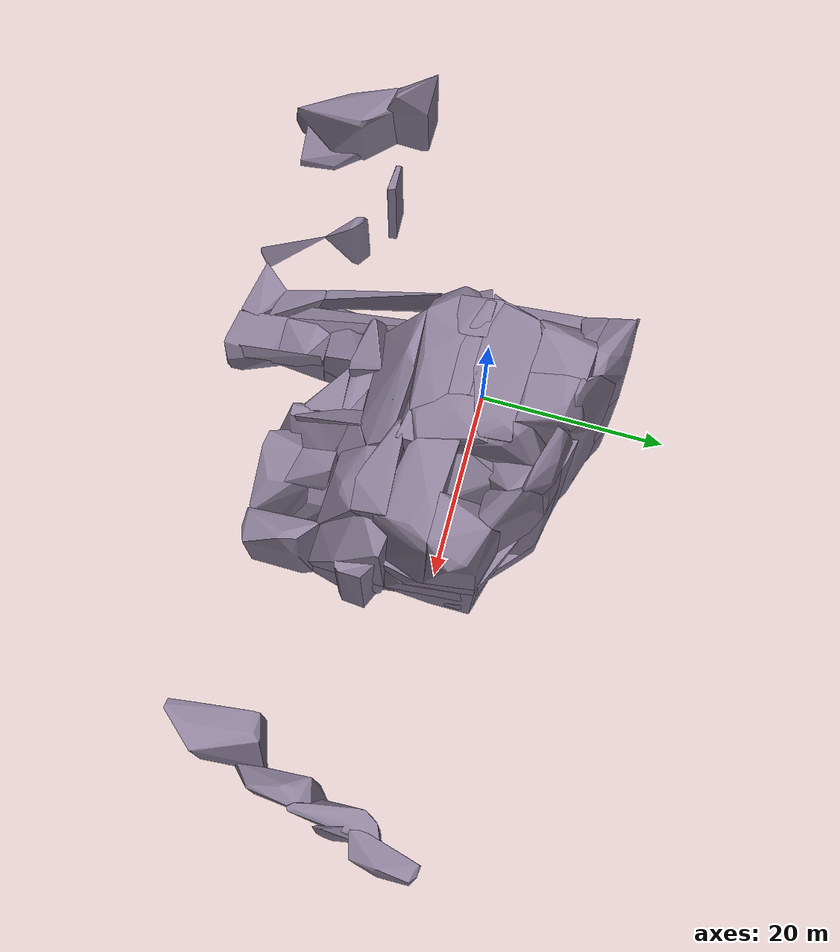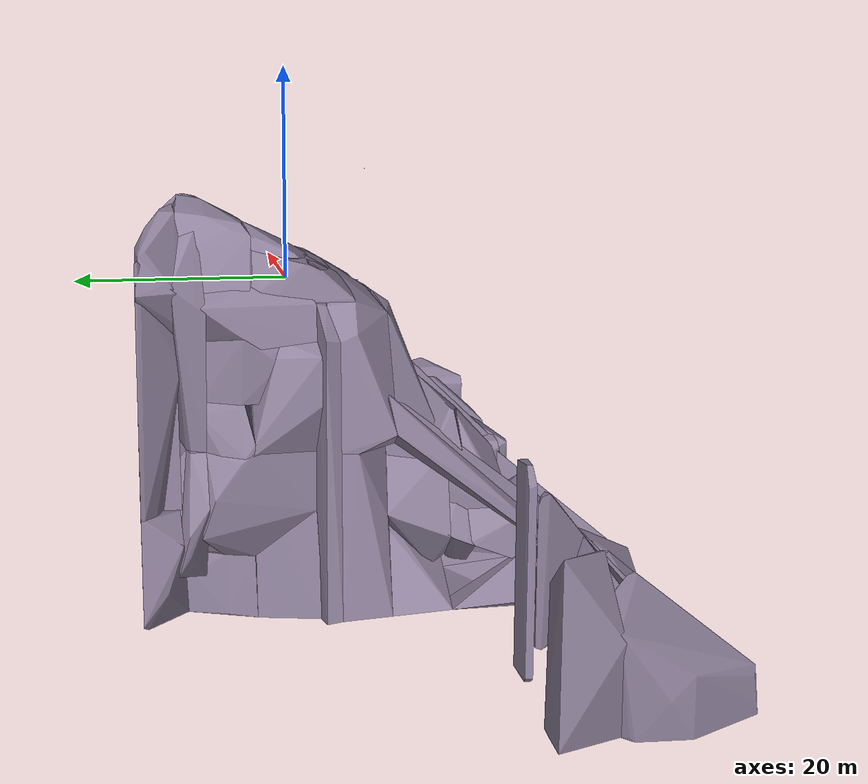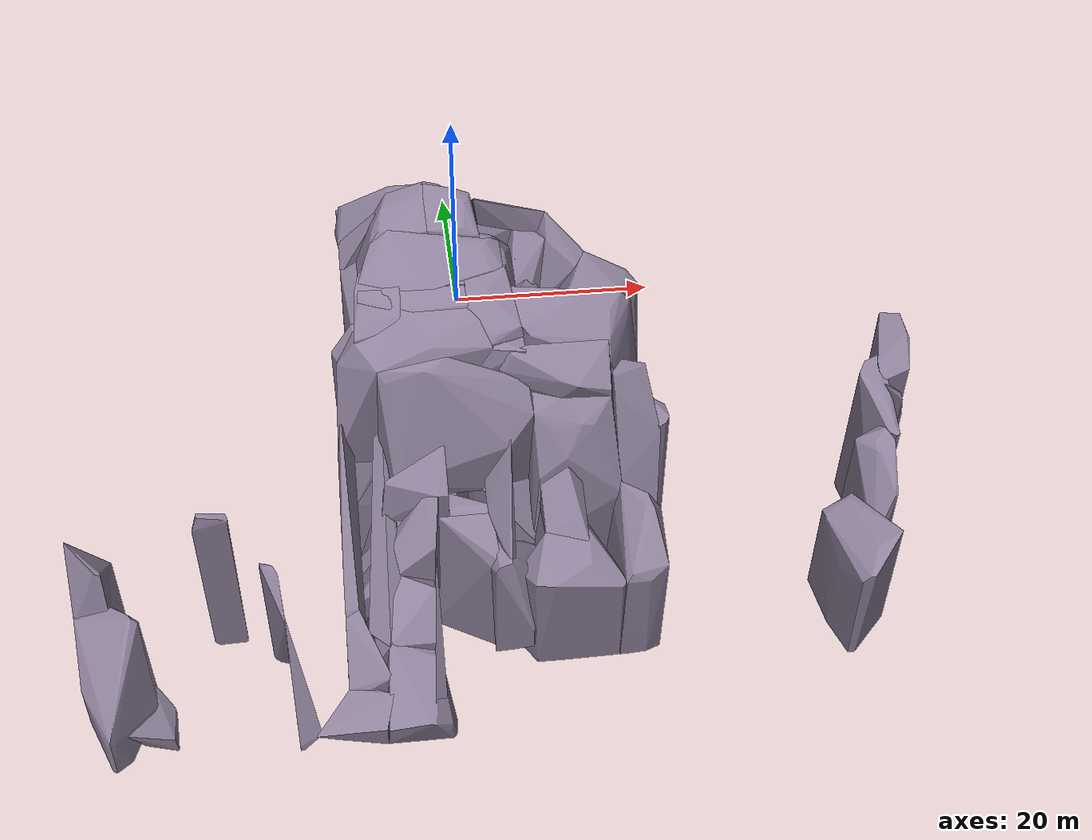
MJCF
<mujoco model="splat_collision">
  <compiler angle="radian"/>
  <option timestep="0.002"/>
  <visual><headlight ambient="0.4 0.4 0.4"/></visual>
  <asset>
    <mesh name="part000" vertex="3.23012 -18.4399 -17.5269 7.07992 -20.5417 -21.1056 3.8673 -13.7827 -22.2707 2.27329 -20.2074 -30.5383 1.71033 -21.9341 -18.328 6.24866 -15.7952 -26.3946 7.04514 -16.0551 -21.1056 3.39783 -21.76 -17.3712 1.4088 -13.8062 -22.2249 5.39948 -23.8208 -27.8359 5.15372 -15.8473 -20.2364 6.19005 -15.3901 -21.7486 6.33798 -20.6342 -26.6229 1.85225 -18.4491 -17.5266 3.42898 -21.2682 -17.2519 1.565 -21.892 -30.4424 1.39188 -13.8059 -25.5899 4.24942 -21.0088 -30.1174 5.39796 -23.8223 -25.5925 5.64587 -15.3234 -26.0724 1.2936 -20.6267 -18.8531 2.09601 -21.8837 -17.756 2.34386 -14.1673 -25.8757 1.70109 -20.8772 -30.5096 3.49115 -20.6961 -30.4904 3.31588 -21.9018 -30.3493 4.19074 -21.1849 -30.0994"/>
    <mesh name="part001" vertex="17.8798 4.70403 -14.376 19.6516 -3.8047 -14.9198 19.0806 3.00901 -19.9841 11.0835 7.51602 -19.9838 6.19858 1.83744 -14.3745 17.8598 4.7005 -19.9841 19.1001 2.84268 -14.3769 11.2963 7.77211 -14.3855 11.4698 -5.26768 -19.9979 10.6619 -6.38342 -13.9537 6.11509 2.86402 -14.3756 19.7518 -5.97073 -19.9842 18.6894 -6.14329 -14.3756 6.22841 1.65349 -16.6024 11.0733 7.51481 -14.3753 19.0191 -6.35679 -16.6185 6.64329 3.26537 -16.5428 8.87219 3.19626 -19.9227"/>
    <mesh name="part002" vertex="0.738163 -1.31634 2.72896 0.943197 -3.48546 1.7035 1.23239 -0.850583 2.00139 -2.73205 -1.25166 -5.15194 -10.2657 -2.20278 2.01677 -2.21007 -0.619957 -4.35005 -10.1141 -1.90089 2.35106 -3.56094 -3.94932 -5.26683 -5.90843 -3.76577 1.39176 0.768228 -2.04157 2.45604 -10.0595 -1.13791 2.68896 -3.6248 -3.74661 -5.40358 0.697277 -3.76123 1.32535 -6.07103 -3.30906 1.65666 -2.52465 0.177046 -4.38773 -10.1981 -1.57992 2.47676 -2.36272 0.0792074 -3.14836"/>
    <mesh name="part003" vertex="-4.72269 -15.5971 -12.3264 -3.57765 -16.1823 -12.6333 -3.74366 -16.1116 -25.5871 -12.1228 -20.5366 -25.6088 -11.8586 -20.4699 -22.3254 -12.1017 -15.9652 -23.5819 -3.56515 -15.9176 -12.537 -4.20379 -19.6282 -16.4454 -12.153 -16.2793 -23.9118 -11.8787 -19.6825 -21.8692 -4.78525 -20.4665 -25.5921 -7.94672 -16.0071 -16.6885"/>
    <mesh name="part004" vertex="17.9464 -16.6492 -13.9513 19.2111 -23.0623 -18.2013 19.0807 -15.0677 -27.4231 17.4716 -15.7883 -30.2463 14.609 -23.8621 -30.3391 15.4598 -14.5185 -13.9708 19.4498 -16.1301 -16.3826 19.0624 -22.9613 -30.4921 14.1258 -14.7096 -27.5293 14.8429 -23.7625 -19.6424 18.3376 -18.7389 -14.2781 17.3654 -23.9917 -30.0319 19.4373 -16.7743 -16.0163 19.1607 -16.4848 -30.3374 16.5746 -16.7581 -30.187 14.8308 -14.6814 -16.9301 15.4507 -23.4363 -18.7446 17.487 -18.2995 -14.1862 15.1839 -23.8706 -30.3379 17.3442 -23.7903 -19.5358 18.2128 -15.9013 -30.3582 15.1639 -22.9499 -30.3931"/>
    <mesh name="part005" vertex="15.3694 -7.29123 -5.38871 14.7314 -10.9466 -5.42871 15.1121 -8.88795 -30.6051 6.40838 -6.0408 -30.6298 6.40851 -7.16206 -5.40536 6.19005 -15.3901 -21.7486 15.6554 -5.98426 -19.9788 6.78194 -9.32047 -5.42007 15.7078 -15.157 -15.1996 9.36095 -12.695 -30.3603 12.0347 -5.96503 -30.6302 15.6229 -6.06591 -11.0043 6.77102 -11.2236 -6.97139 15.1743 -14.4282 -27.167 6.68098 -11.0076 -30.4646 6.9632 -5.96043 -11.0103 9.8788 -14.2362 -10.5979 9.6649 -10.6801 -5.45034 13.4015 -12.9349 -30.0758 7.90648 -14.16 -28.0884 11.7765 -13.0328 -30.5033 7.02911 -14.3668 -13.0259 12.793 -12.8172 -7.58236 14.6949 -10.7339 -30.5909 9.42759 -13.9228 -29.0366 11.5882 -12.8187 -7.39429 11.564 -13.7955 -29.2948 8.88075 -12.5597 -8.11631 14.096 -14.168 -27.9478"/>
    <mesh name="part006" vertex="6.16069 2.06859 -6.52377 5.90391 -3.71147 -6.44315 6.42617 -3.72163 -30.6293 2.82603 5.81658 -30.4568 2.76106 0.42035 -6.54254 6.44283 7.51124 -26.7143 5.9241 -3.72933 -6.59118 3.21149 1.86791 -6.50279 2.68822 -4.3061 -9.7444 6.51101 7.59671 -14.3747 5.60397 3.37338 -30.3539 2.79183 7.4727 -14.3778 3.06106 -3.72162 -30.6297 4.17865 5.3996 -30.2212 3.14564 7.59329 -18.8514 5.80137 7.54794 -26.7058"/>
    <mesh name="part007" vertex="11.4495 -19.0682 -16.0401 15.0316 -23.1753 -20.0024 14.3511 -19.1377 -24.1043 4.19074 -21.1849 -30.0994 5.55746 -23.7553 -18.8315 14.5539 -23.7448 -30.4773 12.5366 -17.3121 -20.3255 11.4584 -22.2265 -17.864 4.14156 -20.4488 -19.994 14.9407 -19.4094 -22.2277 12.4172 -21.6336 -30.1093 5.79389 -23.9225 -30.3136 14.4418 -23.7304 -20.1116 7.06681 -19.0887 -16.0198 11.3942 -17.249 -16.4156 14.6569 -23.3641 -30.4941 7.44783 -24.08 -18.9412 14.9628 -20.3322 -21.3591 10.602 -21.6635 -30.2093 8.28987 -23.8379 -30.4519 12.3292 -22.9382 -18.8013"/>
    <mesh name="part008" vertex="-34.4649 -23.588 -18.8604 -33.9359 -23.777 -19.3818 -37.0764 -20.3608 -20.1902 -37.1662 -19.9984 -30.4765 -37.2547 -33.04 -30.0919 -33.8776 -23.3828 -19.5227 -36.8639 -32.8244 -26.1063 -40.9297 -20.3151 -21.2349 -33.0696 -27.2845 -27.8542 -34.88 -22.8749 -18.9592 -40.1984 -26.6738 -30.2961 -34.9196 -23.6579 -18.9351 -33.8875 -23.7637 -30.1539 -35.4286 -32.0063 -30.2272 -36.5155 -32.6489 -26.7323 -37.384 -20.5936 -19.9229 -39.9626 -22.125 -30.2935 -40.1581 -26.6716 -25.2603 -33.7779 -23.3815 -30.059 -34.8682 -22.8229 -30.4173 -36.8517 -33.2165 -30.2371 -40.6433 -24.6009 -26.9791 -39.197 -21.29 -30.2051 -37.3266 -32.8724 -29.065 -36.8636 -32.8323 -26.1241 -39.7435 -21.7511 -30.003 -37.2816 -32.6474 -26.9234"/>
    <mesh name="part009" vertex="-1.62043 -8.06309 -1.23568 6.77102 -11.2236 -6.97139 6.69863 -8.40509 -15.2758 -9.48452 -8.21635 -15.4914 -7.7679 -13.4356 -13.3317 6.34301 -8.65802 -4.2705 -3.33297 -9.51206 -2.11966 2.94484 -12.8664 -15.2342 6.44707 -9.18923 -4.28556 4.13251 -12.8573 -9.63972 -8.76415 -8.48864 -2.24746 6.52876 -11.2444 -15.4974 -7.62945 -12.5201 -15.7371 -1.83936 -8.14593 -1.17597 -9.43937 -9.33623 -15.4927 -7.99074 -9.27664 -3.16369 -4.12555 -9.35816 -1.93043 -8.74527 -8.66031 -2.4827 -4.7483 -8.84032 -1.78085"/>
    <mesh name="part010" vertex="-8.33985 -8.23996 -22.2262 -8.1671 -13.7111 -25.597 -8.14322 -8.20991 -30.5858 -13.6069 -8.19178 -29.7814 -13.7167 -13.8471 -29.4155 -9.11102 -8.0744 -22.2275 -8.10683 -9.24238 -22.2275 -8.14735 -13.8966 -30.0761 -11.2494 -8.12361 -30.2268 -8.76131 -8.84412 -22.2275 -8.07286 -8.89109 -30.5419 -13.5228 -13.7837 -29.4999"/>
    <mesh name="part011" vertex="43.8748 -22.0777 -17.1056 43.8572 -21.7191 -17.2265 37.5283 -15.6513 -19.4884 37.4375 -15.7244 -30.1826 43.8769 -22.0739 -30.0888 43.2785 -13.7067 -26.5435 38.6477 -26.3816 -19.6624 40.8464 -14.8089 -18.1294 43.7709 -18.0957 -26.7667 41.8477 -15.8095 -30.4309 40.9791 -23.4274 -17.7932 37.7501 -22.0734 -30.2479 39.8515 -26.4877 -18.8563 43.2222 -13.7403 -21.2207 43.8461 -21.764 -30.0821 40.8457 -14.7919 -30.1415 39.4577 -26.4033 -18.8626 40.0976 -15.6087 -18.0201 37.9516 -22.1579 -21.819 37.5322 -16.5891 -19.376 39.5591 -26.3876 -30.4026 40.5177 -14.7724 -18.363 40.502 -14.8435 -30.1217 38.8123 -26.267 -30.4123"/>
    <mesh name="part012" vertex="3.04617 -3.20433 1.72203 4.10339 -5.52621 -2.04705 0.522374 -3.74485 -14.3591 -12.9463 -3.60574 -14.3685 -8.76415 -8.48864 -2.24746 -10.938 -2.60999 -1.24046 3.00327 -7.30122 -1.02938 -11.9505 -8.63995 -13.7798 -6.07103 -3.30906 1.65666 0.519572 -8.06433 -14.3846 -12.8533 -5.15169 -3.54667 -10.8601 -5.21546 -0.874551 -3.08485 -7.2983 -0.610554 3.31628 -7.71253 -4.27653 -13.07 -5.23439 -14.3911 -12.8005 -3.60824 -4.21794 -13.5289 -8.65581 -12.6907 -6.06834 -4.19189 1.19745 2.92844 -4.4429 1.07658 -12.889 -7.39439 -8.52789 -2.57506 -6.34919 0.00857749 -3.62746 -6.3608 -0.0284443"/>
    <mesh name="part013" vertex="-3.32711 10.8222 7.51509 -3.94044 11.9069 7.1023 -12.0762 10.7207 0.40302 -9.51557 13.6239 -4.2803 -3.64569 13.5304 -4.29433 -11.7558 13.9813 3.66303 -4.11609 13.4557 4.07774 -6.73817 8.14961 -4.27712 -12.4582 14.2827 0.209829 -6.13771 12.0153 7.02015 -7.47425 14.2636 3.899 -3.5806 10.9425 -4.28136 -9.73161 8.47085 0.415223 -9.84434 8.59466 -4.26422 -12.0774 11.7558 1.20556 -5.11895 14.3757 -4.2803 -6.4155 10.641 6.97075 -5.34758 14.1423 3.87817 -6.84998 13.3228 5.65261 -6.75193 8.17136 0.209541 -7.76419 14.3652 -4.2803 -11.3242 13.3095 4.00893"/>
    <mesh name="part014" vertex="10.5399 8.92606 -5.4171 11.0527 4.13439 -5.40479 11.3604 7.38157 -24.4715 6.27666 10.4807 -24.4699 6.26171 10.4927 -5.4021 6.17818 2.72862 -22.2271 9.51313 9.79961 -24.4707 11.7854 5.93632 -11.0086 9.51074 9.80015 -5.40237 10.8643 3.51791 -24.3698 5.79268 3.39529 -24.4837 6.78465 7.16561 -5.402 11.1489 8.31557 -24.4732 10.9079 8.68061 -15.4973 10.7421 2.78275 -15.5806 11.3663 6.11812 -24.4504 10.0307 3.40668 -24.3616 6.63438 2.96542 -15.5082 6.11509 2.86402 -19.9841 10.9787 8.54897 -19.9542 11.123 8.29229 -11.0128"/>
    <mesh name="part015" vertex="-8.39025 -8.34178 -15.4947 -2.51436 -11.1312 -18.2117 -3.5543 -9.78164 -25.5926 -9.63914 -12.5463 -26.4746 -9.79373 -14.0026 -15.1991 -7.01213 -13.8649 -25.5953 -12.1998 -7.98454 -20.5599 -3.55438 -9.78214 -18.8624 -8.21098 -13.7362 -15.4972 -3.56055 -11.4761 -25.169 -12.1694 -13.9577 -22.9865 -8.33985 -8.23996 -22.2262 -9.48724 -8.1712 -15.5232 -3.70169 -13.9505 -17.7868 -8.77206 -14.1346 -25.5926 -12.2064 -8.73253 -20.9038 -12.1304 -13.6319 -22.6983 -6.16756 -10.4578 -25.598 -3.64405 -12.9815 -20.8165"/>
    <mesh name="part016" vertex="-1.03809 9.94262 8.13089 3.03773 9.6914 5.80069 -4.11609 13.4557 4.07774 0.580704 12.0062 -30.4453 0.777775 9.60361 -30.6298 1.27947 11.9455 2.97289 -1.07013 10.605 7.36593 -0.740843 9.51089 8.10189 3.06047 9.72592 -30.6179 -2.99793 9.90777 -26.6388 -4.02137 13.737 -9.88867 -3.75727 11.6959 7.20306 2.47672 11.1375 -30.4667 -2.96922 13.309 -26.7143 -1.71424 12.8519 3.08841 -3.61727 10.9087 -9.88943 -2.44264 10.333 8.30366 2.20729 10.9008 4.19238 1.26835 11.8039 -30.4276 -2.13564 13.0512 -26.7144 -2.55546 9.73185 8.38249 -3.32711 10.8222 7.51509"/>
    <mesh name="part017" vertex="-2.76184 -13.8111 -17.741 1.38049 -16.0672 -19.1437 2.19193 -13.7336 -26.6338 -4.25769 -15.5951 -30.4748 -12.153 -16.2793 -23.9118 2.12837 -15.242 -24.8817 1.42306 -13.8337 -19.2861 -7.87347 -16.4037 -17.2339 -2.37036 -15.8097 -30.172 -12.1304 -13.6319 -22.6983 -2.3726 -15.794 -17.7412 -3.56817 -15.7926 -30.3855 -8.77206 -14.1346 -25.5926 -12.1667 -14.3435 -23.1403 1.39139 -13.5977 -26.488 -8.21107 -13.7349 -17.7407 -12.1063 -15.5937 -23.4412"/>
    <mesh name="part018" vertex="-9.60666 -7.52409 -9.88875 -7.85825 -20.5924 -19.9109 -8.22144 -13.7348 -22.2279 -9.8731 -14.4399 -23.5492 -11.5844 -23.6756 -23.708 -9.48724 -8.1712 -15.5232 -8.76131 -8.84412 -9.8888 -9.09343 -23.6705 -23.6863 -8.01567 -15.0864 -15.4957 -9.08516 -8.09205 -9.88934 -9.42604 -26.1994 -23.2865 -8.81801 -8.70141 -9.8888 -9.51724 -26.144 -23.336"/>
    <mesh name="part019" vertex="51.5665 5.70432 -9.87075 51.4121 1.71083 -10.3612 51.6444 1.71875 -30.217 49.4107 6.40558 -30.3922 47.3755 -2.33861 -13.293 51.6509 5.70581 -30.2382 49.472 6.36828 -10.0319 50.819 -1.32093 -12.5681 47.9287 -2.59447 -30.6151 51.0953 1.9495 -9.80116 47.5533 0.0687314 -12.3131 50.798 6.38025 -10.2194 50.7861 -1.32642 -30.1651 50.6646 6.28924 -30.4364 49.8989 6.03098 -9.8984 49.4548 6.54518 -10.3849"/>
    <mesh name="part020" vertex="-4.18737 0.0557541 3.45151 -2.53596 0.183877 -4.47426 -2.06336 8.80053 -2.07288 -9.84706 8.63981 -4.29596 -11.5395 -1.6738 -4.28255 -1.76467 6.04665 -4.34192 -10.2659 8.71334 0.0680849 -7.33058 -1.97484 -1.01171 -12.0049 3.37713 -4.78724 -4.22829 8.52339 -4.26938 -2.21033 7.58908 0.189741 -12.0508 8.67955 -0.994735 -7.15703 -1.50031 -4.2867 -11.1026 -1.65749 -0.990399 -2.63462 3.48119 -4.79533 -4.89891 4.19708 2.45379 -2.67806 8.75938 0.0508458 -12.0434 5.66194 -3.3028 -6.62884 0.699536 2.78788 -7.1815 -1.6775 -3.19429 -12.0598 8.1913 -1.44989 -6.10898 3.85011 2.45111 -10.203 4.17552 0.219924"/>
    <mesh name="part021" vertex="17.0571 -1.61896 0.82063 18.1428 -1.41726 -0.408889 5.41585 -0.988376 1.96809 6.46784 -1.5152 -11.008 15.3794 -8.19584 -4.28309 19.5341 -1.25848 -10.011 15.1648 -6.69729 -1.55133 6.46373 -6.92616 -11.0034 17.937 -6.55755 -11.1371 15.0551 -8.16525 -3.26472 17.8696 -1.88641 -0.316593 12.0851 -2.89408 1.22697 19.5662 -1.95446 -11.3528 15.6057 -7.52089 -11.0201 6.14942 -5.60665 0.156636 16.2134 -5.04004 -1.33493 17.6138 -3.1186 -1.54156 15.5107 -3.90823 0.189029 13.8747 -1.57527 1.32426 19.5451 -1.49332 -11.0106 18.36 -4.58776 -11.2621 6.89576 -6.37673 -0.546024 9.38896 -5.31488 0.0065029 14.1523 -1.9915 1.19346"/>
    <mesh name="part022" vertex="0.541185 9.21383 7.96714 2.85466 4.14287 4.97322 3.37113 10.1116 -14.3696 0.816382 9.73465 -14.3756 -2.54696 4.10176 4.6985 1.21535 3.66718 -9.5855 0.977326 11.1619 5.34466 -2.55208 4.38308 5.81575 3.40693 4.86243 -9.90695 0.441597 7.03308 -14.4164 -3.61697 9.86961 -9.89781 2.23256 9.04755 7.37866 1.55565 7.29381 7.16974 2.62482 9.96924 5.54778 3.1899 4.1141 -4.26239 2.79183 7.4727 -14.3778 -1.09025 4.00832 -9.80899 -2.55546 9.73185 8.38249 1.30783 10.7589 6.15288 1.34501 4.61027 5.76963 0.633831 8.67979 7.92701 2.10859 8.10819 7.27429 1.27315 10.9844 5.64858 -2.23596 5.97088 -9.92484 -2.68922 8.24165 7.93099 1.28643 9.91667 6.97075 0.88213 10.8861 6.08786 2.40623 9.8738 6.22312 -1.12323 7.85507 7.6344"/>
    <mesh name="part023" vertex="-2.83384 -4.45048 -14.3649 -2.54418 -8.06704 -14.3775 -2.56838 -2.9774 -30.6299 -9.88233 -1.67704 -30.6176 -9.45278 -8.21507 -14.3706 -8.30687 -1.47629 -16.623 -2.19196 -2.94782 -16.7735 -7.13681 -10.4391 -30.3149 -6.9448 -1.51351 -30.1931 -9.09412 -2.86187 -14.3753 -2.5475 -8.2073 -30.6294 -5.72615 -11.1327 -14.5212 -8.83743 -7.94434 -30.5639 -7.64608 -1.33724 -19.9843 -9.69081 -1.61732 -16.6128 -5.98519 -2.7879 -30.6302 -8.53553 -10.4643 -16.5917 -3.55443 -9.78239 -15.4973 -3.71417 -9.53615 -30.4515"/>
    <mesh name="part024" vertex="4.1715 4.85042 4.60592 6.29524 -3.94437 -0.986471 6.45771 7.53328 -2.03656 2.78377 6.83943 -6.57727 2.76636 -3.40082 -6.38385 3.0862 7.79966 -0.0953343 6.44318 7.51598 1.32839 2.85466 4.14287 4.97322 5.9241 -3.72933 -6.59118 5.50993 8.16993 -6.5237 5.43073 3.38927 3.28883 2.5687 5.97606 4.36914 4.20598 -3.24661 -1.38186 5.87005 4.66593 -6.65603 5.5103 8.17036 1.32805 3.96059 4.23581 4.71424 2.45668 5.01191 4.80826 5.345 1.92269 2.79349"/>
    <mesh name="part025" vertex="17.8598 4.7005 -19.9841 19.0446 -0.560516 -24.4745 17.8374 4.45766 -30.4678 14.0945 5.45334 -30.4825 9.91779 2.24481 -19.8881 12.3653 -0.340558 -30.0193 14.2181 5.45679 -30.3143 19.0793 2.92262 -26.712 17.524 -0.23521 -19.9809 11.0816 6.27041 -19.9828 17.789 -0.339459 -30.6163 11.1065 6.25367 -24.4694 19.0913 2.86166 -24.4707 11.3622 -1.45792 -24.4687 19.0308 -0.483312 -26.7135 16.0286 0.216257 -30.5669 10.0042 3.13392 -23.3114 12.2094 3.01728 -30.0293 11.8955 -0.310326 -19.9385"/>
    <mesh name="part026" vertex="-2.3702 11.0247 -14.3882 -2.39058 5.85189 -14.397 -2.47858 5.51544 -24.4803 -7.04202 14.3641 -24.469 -9.45191 4.00153 -14.3827 -2.96915 13.3092 -24.4709 -5.198 3.58074 -14.3748 -8.65451 10.1228 -14.5022 -9.27636 4.12898 -24.471 -2.96902 13.3095 -19.9841 -5.21199 3.57634 -24.4701 -9.26811 10.9925 -22.2031 -7.03841 14.3005 -19.9831 -8.22877 9.45312 -24.4708"/>
    <mesh name="part027" vertex="3.96059 4.23581 4.71424 4.96185 0.834605 3.19497 4.90573 4.2599 3.56535 -6.10898 3.85011 2.45111 -9.64697 0.123894 3.43951 -2.4343 3.72018 2.55431 -6.64315 4.57196 6.11829 4.89487 4.37183 4.16033 -6.04035 -1.54482 2.61139 -8.83704 4.15324 3.64877 2.84771 2.3906 4.50885 -10.055 -0.264256 3.03836 -5.91983 -1.11643 2.93985 -2.27781 -1.64618 2.67655 3.46548 3.27475 4.72194 -9.48108 2.46343 3.22178 -8.5631 3.95 4.98134 3.64719 0.0843744 3.33418 -5.95678 4.45227 6.02701 -9.09615 2.73534 4.28482 3.98867 0.133494 3.21551 4.70652 0.987684 3.37465 -2.21933 -1.17842 2.92309"/>
    <mesh name="part028" vertex="-2.81044 2.31131 -19.9979 -2.22068 0.635405 -19.9485 -2.54731 4.13087 -30.6302 -9.99481 3.86885 -30.5358 -11.4506 -1.52817 -19.9841 -10.2127 4.0514 -19.9842 -5.98519 -2.7879 -30.6302 -5.20577 3.57829 -19.9833 -11.5542 -2.11619 -30.443 -2.44003 1.09103 -30.6289 -7.64608 -1.33724 -19.9843 -10.5907 2.00976 -30.4795 -10.6074 2.36048 -19.9833 -2.20873 0.671681 -21.0689"/>
    <mesh name="part029" vertex="-7.31972 -1.98244 -1.00344 -7.65643 -4.12132 -0.928431 -9.55953 -4.08229 -30.5968 -13.5801 -2.19698 -30.2624 -13.3939 -2.22376 -3.95976 -9.88233 -1.67704 -30.6176 -7.79056 -3.46657 -14.4102 -11.1026 -1.65749 -0.990399 -12.8005 -3.60824 -4.21794 -7.05914 -0.79153 -8.65635 -10.938 -2.60999 -1.24046 -13.469 -3.66294 -30.0953"/>
    <mesh name="part030" vertex="48.6196 1.73712 -12.3077 47.4786 -9.39362 -15.0095 48.8311 1.74407 -30.3063 45.2629 -0.915279 -30.5047 45.1782 -0.969054 -12.8462 47.0705 -9.52349 -30.4703 46.4276 0.792489 -30.2921 47.1322 -2.68543 -13.0788 45.6876 -9.32633 -30.6287 46.2731 0.733469 -12.5458 47.1271 -8.49653 -14.542 46.6869 -2.92583 -13.1219 45.0807 -6.34559 -19.1135 47.0135 -9.55386 -15.1535 45.1436 -0.495582 -30.0691 46.6368 -9.59679 -30.4862 46.3973 -8.90102 -15.0366 46.0222 0.375982 -12.7945"/>
    <mesh name="part031" vertex="-8.57494 8.34996 -14.3756 -9.66038 -1.60705 -14.3698 -8.89112 7.12655 -24.4686 -9.42168 6.69668 -24.4709 -12.5897 7.69266 -18.403 -9.73646 -1.63274 -19.9772 -12.6064 3.83369 -13.8354 -12.1605 8.90992 -22.04 -9.27636 4.12898 -24.471 -8.57494 8.34996 -16.619 -10.1466 8.32304 -14.4579 -11.4511 -1.52776 -14.3756 -12.1839 8.90581 -22.0475 -12.6232 5.33825 -15.1178 -11.4506 -1.52817 -19.9841 -10.2152 4.04618 -24.4705 -11.3667 7.42809 -15.5413"/>
    <mesh name="part032" vertex="-2.5138 -12.125 -9.20574 -2.50808 -16.1048 -12.6775 -4.73354 -12.7755 -15.4052 -9.32118 -12.4821 -15.8004 -8.85238 -14.8115 -11.6572 -3.57044 -16.2091 -15.4995 -3.57765 -16.1823 -12.6333 -8.66466 -14.4716 -11.4625 -2.4737 -15.5449 -15.4973 -9.51892 -15.6619 -16.0827 -2.60558 -12.2328 -9.22913 -2.51016 -16.1185 -15.4973"/>
    <mesh name="part033" vertex="18.8409 4.38209 -14.3756 19.7518 -5.97073 -19.9842 18.73 4.19992 -30.4455 17.8374 4.45766 -30.4678 17.2582 -5.00633 -26.7766 17.8798 4.70403 -14.376 19.1001 2.84268 -14.3769 18.9475 -6.30877 -25.6062 17.327 -3.52843 -30.4722 18.3558 -5.86064 -19.9382 17.5292 3.82028 -14.3466 18.6943 -0.747818 -30.4679 18.6903 -6.14415 -25.5925 17.5304 -3.29814 -30.3446"/>
    <mesh name="part034" vertex="3.41109 -3.20949 -3.29413 -0.473518 -1.26303 -22.9922 -4.08769 -4.28068 -9.77615 2.16024 -0.80767 -19.9601 -3.01223 -3.43429 -20.934 -0.541403 -4.73538 -23.3943 0.6687 -0.836228 -5.47205 -2.56622 -1.53467 -9.81696 -1.60493 -4.48688 -23.3833 3.26545 -3.74757 -12.1038 3.18248 -1.14789 -9.09383 -2.72575 -3.82857 -21.0217 1.34134 -3.96479 -20.9488 1.86801 -1.25904 -5.7224 3.25859 -2.02306 -10.4535 3.26699 -3.15502 -11.5647"/>
    <mesh name="part035" vertex="-2.7573 11.2052 5.85134 -1.59228 9.0911 5.73982 -2.3702 11.0247 -14.3882 -9.67173 9.71389 -14.3925 -12.0598 8.1913 -1.44989 -2.5348 8.35629 -14.3667 -12.0728 11.2251 0.825952 -8.65451 10.1228 -14.5022 -10.1466 8.32304 -14.4579 -7.31096 8.72407 5.89125 -12.0727 10.1859 0.0112962 -12.0554 9.21029 -0.615129 -6.76572 10.6304 5.81243"/>
    <mesh name="part036" vertex="-5.30357 4.25665 -9.86878 -1.63709 1.69492 -11.1663 -2.81044 2.31131 -19.9979 -9.34543 4.16397 -19.9844 -9.59671 -1.49066 -9.87975 -5.20577 3.57829 -19.9833 -2.55853 -1.47721 -9.88953 -8.99203 4.18954 -10.0008 -9.73646 -1.63274 -19.9772 -2.66127 0.419953 -9.90121 -2.22068 0.635405 -19.9485 -7.64608 -1.33724 -19.9843 -2.53739 -1.91538 -10.561"/>
    <mesh name="part037" vertex="7.03481 -14.9335 -16.6188 14.9139 -18.2883 -23.3494 15.1566 -15.2282 -26.038 9.42744 -14.4833 -28.4907 6.30648 -19.4749 -25.5426 12.4057 -14.8456 -20.0774 7.06967 -19.4287 -16.6192 5.61167 -16.5281 -25.0495 12.3909 -19.7392 -26.4298 14.1258 -14.7096 -27.5293 9.17067 -14.7538 -17.987 15.1875 -16.508 -25.1436 12.569 -19.3848 -19.9187 7.76483 -14.6884 -27.557 9.13688 -19.8093 -26.3045 14.9411 -19.4731 -25.5277 14.2161 -19.6693 -23.6609"/>
    <mesh name="part038" vertex="46.1828 -8.34194 -14.905 46.9072 -9.65504 -15.5041 46.0509 -7.44695 -30.6176 43.0821 -7.49499 -30.2842 43.37 -17.2142 -23.3509 45.1208 -5.5615 -20.8837 45.8019 -14.7442 -18.6259 45.7237 -14.9445 -30.1497 43.1618 -7.85113 -16.6116 46.4054 -5.85712 -21.1062 45.1325 -11.0133 -16.2013 43.7562 -17.544 -26.3061 45.7487 -14.6266 -30.291 46.1354 -14.8289 -30.0631 46.0348 -7.04761 -15.5327 43.215 -13.2058 -20.8523 46.7769 -9.13266 -30.6177 46.3973 -8.90102 -15.0366 44.7981 -9.46141 -15.7593 44.708 -10.5358 -16.2162 43.2643 -13.1683 -26.9032 43.1413 -8.51412 -30.0129 46.1248 -14.8441 -18.8877 44.7046 -8.17476 -15.6887 46.3115 -6.1641 -17.7368 43.183 -8.24923 -16.8029 45.802 -15.0268 -18.953"/>
    <mesh name="part039" vertex="-3.5543 -9.78164 -25.5926 -4.78525 -20.4665 -25.5921 -4.62174 -20.4695 -30.124 -7.13685 -10.4364 -30.3149 -9.95861 -20.4542 -25.8509 -3.59976 -10.1551 -28.8588 -6.16756 -10.4578 -25.598 -10.4279 -20.5656 -29.3549 -4.83219 -14.9751 -30.5027 -9.64588 -13.6446 -26.6568 -6.99349 -20.5482 -30.3391 -6.63869 -10.4721 -30.1581 -10.4266 -19.4464 -29.4081 -8.63548 -14.388 -30.5013"/>
    <mesh name="part040" vertex="6.29524 -3.94437 -0.986471 6.35285 -8.02454 -1.28055 6.34779 -6.29971 -24.4858 0.781663 -4.99696 -24.4778 0.738107 -7.93368 -4.30155 6.66429 -3.71733 -12.1002 2.48342 -5.52855 -0.67998 6.32533 -8.1762 -24.4784 5.03577 -5.99094 -24.522 1.28783 -3.1864 -7.31053 3.07479 -7.43231 -1.24109 0.733066 -8.25099 -24.4719 4.37118 -3.25433 -0.984416 0.522123 -4.98387 -23.4054 0.807613 -7.17024 -4.27977"/>
    <mesh name="part041" vertex="14.0647 4.72639 1.9959 19.371 1.37193 -0.197159 18.8094 4.41735 -11.0119 10.7332 1.20036 -11.2626 11.4878 -1.65801 1.50192 19.5451 -1.49332 -11.0106 14.0626 5.7624 -11.0106 18.824 4.19357 -1.61891 17.0571 -1.61896 0.82063 11.1485 3.42222 -1.55171 11.0973 -1.69557 -11.0105 18.3802 3.1604 0.405224 13.8018 5.6463 -0.144318 13.8747 -1.57527 1.32426 18.711 -0.702815 -1.05961 11.477 -1.55069 1.47311 11.021 2.65267 -8.93533 18.3587 2.41147 0.544912 14.0169 4.36035 1.98713"/>
    <mesh name="part042" vertex="-41.2324 -15.7863 -15.1647 -37.2782 -20.1128 -16.0426 -37.1658 -15.8547 -30.0238 -41.2085 -15.7896 -30.1736 -40.8939 -20.8519 -21.9543 -37.0878 -16.0441 -18.3734 -37.8806 -19.9625 -15.8011 -37.1662 -19.9984 -30.4765 -37.3943 -19.8086 -15.9404 -37.0095 -21.6274 -21.1789 -39.197 -21.29 -30.2051 -37.3438 -16.0272 -30.4488 -37.0701 -16.5509 -30.4743"/>
    <mesh name="part043" vertex="-5.43075 14.4479 -19.9953 -2.56429 10.9619 -24.4712 -2.91542 13.0803 -30.4551 -11.8363 13.9138 -30.4345 -12.5486 10.5781 -22.4292 -5.38515 14.3451 -30.2732 -2.96915 13.3092 -24.4709 -7.10317 10.9249 -19.9806 -12.3511 14.3505 -19.9825 -7.65876 10.1753 -30.5143 -4.78363 13.6421 -19.999 -12.2878 14.3581 -30.0884 -9.76386 10.8154 -20.0035 -2.56207 10.9437 -30.6281 -12.1993 12.0705 -27.0761 -12.2101 13.9714 -20.0147 -11.0109 12.9931 -30.3354"/>
    <mesh name="part044" vertex="-9.43065 -25.6769 -22.9292 -3.81171 -32.4312 -28.457 -5.19415 -26.1317 -30.2242 -9.97906 -28.8761 -30.497 -10.1286 -32.7719 -28.2095 -3.38432 -32.106 -30.4887 -10.4346 -26.1082 -29.0915 -4.57358 -26.0439 -24.625 -6.05745 -33.3211 -27.0728 -6.91399 -26.1556 -30.3525 -10.3186 -32.6025 -30.4145 -9.52905 -25.6254 -22.9885 -3.32109 -30.6764 -30.0666 -9.39455 -29.7729 -25.7294 -4.60793 -27.1818 -24.5685 -3.78889 -32.7002 -30.314 -3.46892 -30.9962 -30.4518 -3.77006 -32.2018 -28.5066 -5.47629 -33.3526 -27.1698 -3.41638 -30.6409 -29.6564 -4.02948 -32.7537 -29.0509"/>
    <mesh name="part045" vertex="6.69863 -8.40509 -15.2758 7.04514 -16.0551 -21.1056 6.42635 -8.2083 -30.629 -0.3041 -8.2073 -30.6289 1.74727 -14.3177 -14.757 6.2551 -15.253 -26.84 -0.210534 -8.35683 -15.4961 6.68098 -11.0076 -30.4646 6.52876 -11.2444 -15.4974 1.39272 -14.9276 -21.1031 -0.0710927 -9.81354 -30.5383 -0.0640034 -10.0873 -15.5029 4.61183 -15.4715 -26.0058 2.32554 -10.5626 -30.3172 -0.134377 -10.0754 -17.7441 2.17182 -14.2107 -26.0796 1.39943 -13.037 -27.0504"/>
    <mesh name="part046" vertex="-2.44264 10.333 8.30366 -2.55208 4.38308 5.81575 -4.13097 8.46529 0.214565 -9.80769 10.8395 0.221547 -8.5631 3.95 4.98134 -2.7573 11.2052 5.85134 -3.42142 8.00873 7.8346 -6.4155 10.641 6.97075 -4.9572 4.23285 0.212472 -7.07493 10.9058 0.206221 -2.54696 4.10176 4.6985 -7.56302 4.67895 5.95172 -2.68922 8.24165 7.93099 -8.80679 11.0009 3.18463 -7.17051 7.95027 6.64855 -10.203 4.17552 0.219924 -10.2659 8.71334 0.0680849 -2.53156 4.13669 4.89271 -3.75885 6.52519 0.172654 -9.64668 3.92349 1.39467 -8.21137 5.73249 5.49164 -6.76227 10.6256 6.59448"/>
    <mesh name="part047" vertex="-12.8697 -7.97197 -9.04122 -11.8575 -22.9466 -24.2603 -11.9505 -8.63995 -13.7798 -13.8361 -23.1282 -24.0693 -12.3919 -22.2575 -21.7378 -13.5289 -8.65581 -12.6907 -11.8441 -8.71563 -12.9978 -13.81 -21.8849 -22.1486 -11.857 -7.97419 -12.4669 -13.0164 -7.88667 -9.11191 -13.7584 -19.4492 -19.9838"/>
    <mesh name="part048" vertex="10.0859 6.87606 5.85855 14.0647 4.72639 1.9959 10.9794 8.47183 2.22248 10.9079 8.68061 -11.0105 8.94069 2.80554 -2.96849 14.0626 5.7624 -11.0106 9.3726 8.92844 3.14963 10.8171 7.66474 4.12717 12.943 2.8947 1.16451 13.9448 5.03025 1.24718 10.0912 9.49733 -6.56632 12.4058 3.00901 -11.0105 9.18287 7.84921 5.14114 10.4374 7.4474 4.92234 10.7015 8.42042 3.0484 13.9062 4.36846 2.11633 10.0714 5.00855 3.38257 9.77976 9.72316 -5.40199 10.8395 4.64878 -11.0106 11.021 2.65267 -8.93533 10.2868 6.74148 5.71507 14.5725 3.53976 -11.0105 11.123 8.29229 -11.0128 13.286 2.88376 1.19584 10.3423 2.73093 -5.09597"/>
    <mesh name="part049" vertex="-4.22829 8.52339 -4.26938 -2.6647 -1.40764 -4.25919 -2.53445 8.50996 -9.88558 -9.59732 8.82436 -9.86137 -12.0386 4.932 -3.83753 -7.40163 -3.96023 -9.5648 -2.26526 8.676 -5.42118 -2.61822 4.9024 -3.92173 -9.84706 8.63981 -4.29596 -2.58658 -2.3558 -10.1546 -11.2291 1.37134 -9.86906 -9.52344 -1.56081 -4.27658 -3.8685 -4.02778 -7.70559 -11.2933 5.16163 -9.92844 -9.59671 -1.49066 -9.87975 -12.0175 1.67269 -6.22517 -4.93467 -3.93081 -9.59633 -7.72323 -3.79526 -7.64214 -11.9985 2.63509 -5.31798"/>
    <mesh name="part050" vertex="-8.65451 10.1228 -14.5022 -8.57494 8.34996 -14.3756 -6.6835 8.70784 -24.475 -7.72902 10.485 -26.7157 -12.5562 10.0471 -21.6882 -7.03455 10.9611 -24.4708 -10.1466 8.32304 -14.4579 -8.55524 8.47845 -26.7157 -7.02893 10.9633 -26.7142 -12.1944 11.0592 -25.4692 -9.67521 9.7555 -14.6045 -12.5821 8.22373 -19.144 -6.70798 8.70154 -26.7181 -8.22858 9.45307 -26.7142 -12.1889 9.91711 -23.6544"/>
    <mesh name="part051" vertex="-9.67277 1.79418 -4.14915 -9.52344 -1.56081 -4.27658 -9.45191 4.00153 -14.3827 -12.5995 4.17003 -14.3493 -13.386 -1.89374 -5.40237 -8.99203 4.18954 -10.0008 -11.5395 -1.6738 -4.28255 -11.9939 2.10435 -5.69758 -9.66038 -1.60705 -14.3698 -12.6417 4.04055 -13.3071 -10.2142 4.05144 -9.8888 -11.191 1.43346 -4.27941 -13.2799 -1.90929 -9.87544 -11.4511 -1.52776 -14.3756 -13.3231 -1.90348 -7.63579"/>
    <mesh name="part052" vertex="-4.49154 -22.201 -19.4936 -4.59834 -26.0551 -23.4519 -4.62174 -20.4695 -30.124 -11.9613 -20.5536 -30.0476 -9.42604 -26.1994 -23.2865 -6.91399 -26.1556 -30.3525 -7.8686 -20.0653 -19.5397 -5.19415 -26.1317 -30.2242 -6.99349 -20.5482 -30.3391 -11.8736 -26.1608 -30.0521 -4.61648 -20.1672 -20.5278 -9.61094 -22.0294 -20.5785 -12.0381 -26.2127 -27.701 -9.16068 -20.3668 -21.3577"/>
    <mesh name="part053" vertex="15.4686 -5.99582 -4.27839 20.0115 -11.6434 -10.0443 19.7518 -5.97073 -19.9842 15.6554 -5.98426 -19.9788 14.8362 -14.9515 -19.9839 19.0216 -6.51566 -4.96941 15.1539 -10.388 -5.39989 15.1458 -9.23026 -4.30956 19.5313 -14.6672 -19.8686 15.4598 -14.52 -13.9717 18.9766 -6.96282 -4.9379 19.4659 -15.0581 -17.8339"/>
    <mesh name="part054" vertex="2.78722 7.11083 -9.92034 3.40693 4.86243 -9.90695 2.79183 7.4727 -14.3778 -11.3539 7.03362 -14.5644 -11.1987 4.97539 -9.55195 3.18494 4.24657 -14.3692 -9.61505 9.03634 -10.9412 1.21535 3.66718 -9.5855 -12.6286 4.95764 -14.5867 -2.53445 8.50996 -9.88558 -10.1466 8.32304 -14.4579 3.20975 4.15103 -12.133 -11.2984 5.31886 -10.3178 -12.6416 4.04597 -13.3146 -2.5348 8.35629 -14.3667 -9.34857 8.70734 -9.87262 -12.5995 4.17003 -14.3493"/>
    <mesh name="part055" vertex="0.856285 1.75357 3.68851 3.5975 -0.00676508 -0.437679 1.65169 4.91196 -11.1066 -2.15536 1.95637 -14.5183 -2.21933 -1.17842 2.92309 2.9764 -1.27589 -14.4074 -2.64883 5.20737 -3.21043 3.26885 4.06375 -3.16437 0.738163 -1.31634 2.72896 3.01557 1.94006 -14.4832 -2.53739 -1.91538 -10.561 0.00317485 5.30506 -12.1741 -2.54421 3.90755 3.6115 3.2445 4.15578 -5.40296 0.333734 -1.4267 -14.4113 -2.28044 0.454027 -14.3465 -0.989247 3.90037 3.448"/>
    <mesh name="part056" vertex="14.9741 -6.72574 -1.40711 14.7317 -10.9149 -4.69226 15.3694 -7.29123 -5.38871 6.40851 -7.16206 -5.40536 5.00852 -8.31343 -1.50228 14.7314 -10.9466 -5.42871 11.3251 -11.189 -3.82509 6.54181 -7.20033 -1.06177 9.6649 -10.6801 -5.45034 14.7193 -7.2777 -1.7046 3.22826 -7.6747 -3.28938 4.14954 -8.54039 -3.29111 4.75958 -7.87084 -1.31859 4.11185 -8.62337 -4.37122 9.84825 -10.724 -3.49232 3.31628 -7.71253 -4.27653 6.4745 -9.20806 -5.40462"/>
    <mesh name="part057" vertex="3.37113 10.1116 -14.3696 2.9764 -1.27589 -14.4074 3.28602 -0.795636 -30.6301 0.777775 9.60361 -30.6298 0.34435 -1.51571 -14.3491 3.06047 9.72592 -30.6179 0.816382 9.73465 -14.3756 1.26231 -0.12885 -30.6297"/>
    <mesh name="part058" vertex="18.8094 4.41735 -11.0119 18.6899 -6.14619 -11.011 19.6406 -3.56699 -14.4615 6.11509 2.86402 -14.3756 6.15139 2.78612 -11.0066 6.63834 -6.0748 -13.1284 18.8409 4.38209 -14.3756 19.5662 -1.95446 -11.3528 14.3567 5.50569 -11.0032 18.6894 -6.14329 -14.3756 6.9632 -5.96043 -11.0103 11.0504 6.29133 -14.3745 6.96377 -4.1028 -14.2821 11.0317 6.30389 -11.0096 14.2724 5.57884 -14.3646 9.07867 -5.17821 -14.2747"/>
    <mesh name="part059" vertex="0.663309 9.81906 -9.90059 1.42085 6.98034 -9.88443 0.792358 9.65328 -24.4702 -2.67606 9.78737 -24.4494 -3.61697 9.86961 -9.89781 -2.7538 2.76339 -23.3801 0.945591 4.61958 -24.4884 -2.52456 7.54527 -9.88973 1.04168 7.42363 -24.4604 1.03359 4.95603 -14.405 -2.20432 5.44237 -24.5177 -2.39058 5.85189 -14.397"/>
    <mesh name="part060" vertex="4.26627 -12.5349 -8.8001 1.41656 -12.4852 -13.5538 2.94192 -20.7367 -17.9622 3.42898 -21.2682 -17.2519 2.94484 -12.8664 -15.2342 3.8149 -21.0477 -17.9701 1.46304 -15.8425 -15.8079 4.22079 -12.5341 -9.01355 3.19464 -21.1576 -17.3816 3.12775 -16.5135 -16.7522 1.43978 -13.4591 -14.3237 2.99936 -14.0974 -15.7805"/>
    <mesh name="part061" vertex="6.34779 -6.29971 -24.4858 6.32533 -8.1762 -24.4784 6.42635 -8.2083 -30.629 -2.56838 -2.9774 -30.6299 -2.63532 -4.09684 -26.731 6.42632 -3.72078 -30.6293 0.781663 -4.99696 -24.4778 -2.54901 -8.28005 -30.0785 3.02303 -3.28751 -30.6294 0.733066 -8.25099 -24.4719 -2.5475 -8.2073 -30.6294 -1.42685 -8.25983 -26.7136 -2.51382 -4.75747 -26.7156"/>
    <mesh name="part062" vertex="-20.5491 -20.3304 -16.3655 -19.7041 -24.2522 -20.8332 -20.2503 -20.4125 -30.0699 -21.9043 -19.9966 -30.3469 -21.719 -20.5043 -16.2466 -20.342 -21.2052 -30.262 -21.6514 -19.3821 -30.0615 -20.0694 -21.0867 -16.7712 -21.6102 -20.5984 -30.0754 -21.6225 -19.5355 -30.2626 -21.2619 -19.7629 -16.5794 -21.9986 -19.3746 -17.2023 -19.784 -23.1554 -19.4867 -21.2025 -20.786 -30.3253 -22.023 -19.3765 -30.0791 -21.9065 -19.7319 -16.4374 -19.7808 -23.1954 -19.5315"/>
    <mesh name="part063" vertex="5.345 1.92269 2.79349 6.48168 -5.86696 -0.914893 6.19828 1.84762 -0.807417 0.752321 0.592129 -0.918607 0.768228 -2.04157 2.45604 3.85389 -6.76892 -1.06702 0.856285 1.75357 3.68851 6.14942 -5.60665 0.156636 3.09954 1.37276 -0.957127 0.697277 -3.76123 1.32535 5.17847 0.868439 2.97698 2.96249 -7.12274 -0.896517 0.758035 1.23071 3.12265 3.13601 -6.49344 -0.177353 2.96885 -2.09912 2.42221 0.943197 -3.48546 1.7035 3.83701 -6.3922 -0.150077 2.92844 -4.4429 1.07658"/>
    <mesh name="part064" vertex="1.92685 -15.8999 -15.7314 2.30785 -20.7992 -18.0317 2.27329 -20.2074 -30.5383 -3.56817 -15.7926 -30.3855 -3.6943 -16.1839 -15.4977 -4.58381 -17.0472 -30.3191 2.10502 -15.7962 -24.2379 -3.57044 -16.2091 -15.4995 1.70109 -20.8772 -30.5096 1.2936 -20.6267 -18.8531 -2.37036 -15.8097 -30.172"/>
    <mesh name="part065" vertex="-3.64569 13.5304 -4.29433 -2.1068 11.0823 -9.91761 -2.96902 13.3095 -19.9841 -9.2758 13.5855 -19.9841 -9.93463 10.8344 -4.26166 -9.38439 10.6379 -20.0261 -5.43075 14.4479 -19.9953 -1.7811 12.8879 -12.1249 -3.5806 10.9425 -4.28136 -9.51557 13.6239 -4.2803 -2.56649 10.975 -19.9845 -7.76774 14.3638 -19.9841 -5.11895 14.3757 -4.2803 -1.7137 12.8765 -14.3942 -7.76419 14.3652 -4.2803"/>
    <mesh name="part066" vertex="9.89296 -14.7825 -11.1594 11.4671 -20.382 -16.8865 11.3577 -15.3024 -15.684 7.03481 -14.9335 -16.6188 7.06681 -19.0887 -16.0198 11.3935 -14.8871 -13.3466 9.993 -18.645 -15.1294 7.03316 -14.874 -13.3475 7.0696 -19.42 -16.6188 9.94152 -14.7362 -11.2417"/>
    <mesh name="part067" vertex="11.0973 -1.69557 -14.3756 10.9772 -4.76262 -14.3772 11.2651 -2.76338 -30.5374 6.20187 -0.360356 -30.4628 6.35814 -0.432129 -14.3764 6.40838 -6.0408 -30.6298 11.1883 -1.60477 -25.589 11.4698 -5.26768 -19.9979 9.07867 -5.17821 -14.2747 6.36083 -2.12024 -14.3557 10.9195 -5.92736 -30.6303 6.96377 -4.1028 -14.2821 9.91632 -6.57888 -14.3347 6.40302 -6.06381 -30.0838"/>
    <mesh name="part068" vertex="8.07278 4.22222 -0.259751 11.1734 -1.62517 -3.16409 11.0597 3.01287 -6.52663 6.59617 1.67871 -11.0695 6.49419 -1.47561 -1.15594 11.0973 -1.69557 -11.0105 8.7799 4.44837 -1.23207 6.38475 0.529356 0.184686 11.2285 -0.64374 -3.22077 10.7332 1.20036 -11.2626 6.46784 -1.5152 -11.008 6.88007 4.29993 -1.19047 8.39167 -1.33927 -1.57053 8.22239 4.23276 -0.320984 11.1045 3.01405 -4.28413 6.11492 2.86442 -6.52364 6.13362 2.82331 -0.931421"/>
    <mesh name="part069" vertex="-33.9697 -23.8936 -27.8359 -31.2449 -30.9847 -28.7712 -31.5706 -26.6626 -30.1793 -35.0692 -23.7358 -30.5172 -35.9325 -31.1992 -27.1983 -34.4362 -30.0212 -30.4953 -33.8875 -23.7637 -30.1539 -31.5721 -26.6952 -29.0825 -35.1517 -23.9146 -27.8361 -31.2406 -30.9978 -30.4492 -33.7891 -23.7236 -28.9577 -31.0676 -31.0121 -30.3407"/>
    <mesh name="part070" vertex="-12.3926 -22.2366 -21.7192 -9.45838 -28.7287 -25.0682 -10.0388 -26.0941 -28.0093 -11.9262 -22.7965 -30.0494 -13.9989 -28.3846 -28.4749 -13.9354 -27.7984 -27.4115 -10.123 -28.6193 -30.0799 -13.8218 -22.4418 -22.6442 -10.4346 -26.1082 -29.0915 -13.3429 -22.7329 -29.0683 -13.8905 -22.8016 -28.8362"/>
    <mesh name="part071" vertex="14.1339 5.69772 -24.4494 14.7713 3.30315 -24.4119 14.7502 3.72436 -30.4771 6.014 10.3758 -30.4649 6.7108 5.53885 -24.3854 9.39096 9.82676 -30.032 8.18768 5.22172 -24.1335 6.27666 10.4807 -24.4699 12.2116 2.96861 -30.0291 14.0945 5.45334 -30.4825 10.0307 3.40668 -24.3616 9.51313 9.79961 -24.4707 6.90544 7.40667 -30.4941 10.7737 8.58519 -30.3435 10.948 8.60565 -24.479 6.79143 6.42271 -27.4935 9.95947 5.1213 -30.3089 8.23765 9.67152 -30.4562"/>
    <mesh name="part072" vertex="-19.7392 -23.7111 -20.109 -16.8363 -31.1166 -29.9145 -19.6637 -24.7684 -21.4287 -19.0747 -32.302 -30.1195 -19.0357 -32.6808 -29.4525 -18.6464 -32.6663 -30.0777 -19.0179 -32.6585 -30.1283"/>
    <mesh name="part073" vertex="-11.8623 -22.2119 -23.7221 -13.5228 -13.7837 -29.4999 -10.4197 -13.7973 -29.6766 -13.7167 -13.8471 -29.4155 -11.9262 -22.7965 -30.0494 -13.8919 -22.8738 -28.8315 -10.4279 -20.5656 -29.3549 -12.0201 -22.6055 -26.0964 -11.8623 -22.2166 -23.7256"/>
    <mesh name="part074" vertex="-5.94115 3.81188 3.57716 -5.73664 -4.88791 0.657992 -6.11093 3.84608 -0.915189 -10.2053 4.0512 -0.915265 -10.4568 -0.826508 2.56015 -5.63256 -5.35597 -1.0402 -8.84899 4.08067 3.73815 -5.91983 -1.11643 2.93985 -10.8601 -5.21546 -0.874551 -10.143 0.71069 2.93528 -10.162 -2.35058 1.90339 -10.4799 2.47069 -0.919793 -10.8724 -5.21439 -0.694527 -10.2824 3.15959 0.205168 -6.06834 -4.19189 1.19745 -6.82086 -4.04527 1.22131"/>
    <mesh name="part075" vertex="-9.31972 -3.75064 -14.3987 -9.45278 -8.21507 -14.3706 -8.83743 -7.94434 -30.5639 -13.469 -3.66294 -30.0953 -13.07 -5.23439 -14.3911 -9.55953 -4.08229 -30.5968 -12.9463 -3.60574 -14.3685 -13.6083 -8.26402 -29.7768 -11.2494 -8.12361 -30.2268 -12.1998 -7.98454 -20.5599 -13.4103 -5.90013 -29.9932"/>
    <mesh name="part076" vertex="-0.210534 -8.35683 -15.4961 -0.0640034 -10.0873 -15.5029 -0.0710927 -9.81354 -30.5383 -3.66921 -8.2073 -30.6297 -3.72094 -14.2918 -16.7813 -0.3041 -8.2073 -30.6289 -3.55443 -9.78239 -15.4973 -2.38919 -14.4146 -22.7331 -3.66565 -8.05683 -15.4994 -2.77078 -14.1171 -16.7216 -4.35388 -15.0799 -23.3632 -3.71417 -9.53615 -30.4515"/>
    <mesh name="part077" vertex="48.449 -5.23896 -12.5931 48.4472 -6.14742 -12.9108 48.9613 -4.35805 -30.186 47.9287 -2.59447 -30.6151 47.3755 -2.33861 -13.293 47.6961 -6.6212 -30.4524 48.9701 -5.60722 -15.564 48.4224 -5.27181 -12.591 48.6888 -1.95837 -14.1584 48.4233 -6.19781 -30.489 48.5534 -1.95359 -30.4815 48.8713 -5.50165 -30.378"/>
    <mesh name="part078" vertex="7.95343 9.865 3.40135 9.93883 5.36505 3.46755 9.51074 9.80015 -5.40237 6.26171 10.4927 -5.4021 6.13362 2.82331 -0.931421 9.32342 9.78563 1.77653 6.7844 7.16719 3.57111 8.61835 2.45964 -4.83344 6.15795 10.2175 3.43848 9.3726 8.92844 3.14963 10.1807 4.87149 -5.39827 8.27965 2.87991 -0.631218 6.11509 2.86449 -5.40194 8.94069 2.80554 -2.96849"/>
    <mesh name="part079" vertex="-10.486 13.8274 3.45449 -8.77699 13.7242 0.230722 -12.0995 14.3077 3.03078 -12.3511 14.3505 -19.9825 -9.99576 10.4809 -6.91999 -11.39 14.3551 -19.9842 -9.80769 10.8395 0.221547 -11.9891 13.7442 0.206677 -9.27758 12.277 -19.9841 -12.07 14.0326 3.24654 -12.2101 13.9714 -20.0147 -9.2758 13.5855 -19.9841 -9.0554 10.4717 -6.86183 -10.6676 13.8584 3.48337 -11.0707 12.917 -19.9841"/>
    <mesh name="part080" vertex="1.7946 -15.0986 -15.2635 1.92685 -15.8999 -15.7314 -4.62321 -12.7002 -17.7764 -8.54552 -12.6757 -17.7732 -8.01567 -15.0864 -15.4957 -2.3726 -15.794 -17.7412 -4.76367 -11.823 -15.1685 1.79976 -16.3834 -16.1418 -7.87347 -16.4037 -17.2339 -8.53947 -11.3369 -17.0579 -7.63333 -11.7792 -15.206 -2.4737 -15.5449 -17.7407"/>
    <mesh name="part081" vertex="-9.42895 -30.021 -25.9343 -10.3357 -32.662 -28.1761 -9.97906 -28.8761 -30.497 -15.7066 -30.6555 -30.4395 -17.4739 -31.4614 -29.7729 -10.3358 -32.5185 -30.5628 -13.9351 -27.7851 -27.3997 -15.1453 -31.6801 -30.2677 -11.5053 -28.2338 -26.9714 -11.8388 -28.387 -30.0538 -17.0061 -31.2991 -30.0429"/>
    <mesh name="part082" vertex="0.257926 12.21 -26.7142 0.886963 -0.145977 -26.7068 0.580704 12.0062 -30.4453 -2.65833 12.8134 -30.5369 -2.14897 0.853059 -26.6709 0.928919 -0.0190016 -30.6296 -2.32917 13.1034 -26.7015 -2.10664 0.981177 -30.629"/>
    <mesh name="part083" vertex="-2.56429 10.9619 -24.4712 -2.47858 5.51544 -24.4803 -2.56207 10.9437 -30.6281 -7.65876 10.1753 -30.5143 -10.2152 4.04618 -24.4705 -7.03455 10.9611 -24.4708 -5.21199 3.57634 -24.4701 -9.42168 6.69668 -24.4709 -2.54744 4.13057 -30.6302 -7.72902 10.485 -26.7157 -9.30608 6.56548 -30.3147 -9.99481 3.86885 -30.5358 -8.22858 9.45307 -26.7142"/>
    <mesh name="part084" vertex="-4.20236 -20.1873 -16.9879 -4.17317 -31.5724 -28.0346 -4.78525 -20.4665 -25.5921 -5.26787 -27.162 -27.8352 -5.48459 -32.4763 -27.1789 -4.79102 -20.5467 -25.5926 -5.27364 -27.2422 -27.8358 -4.86103 -32.2268 -28.0874"/>
    <mesh name="part085" vertex="10.0859 6.87606 5.85855 10.0538 6.47675 3.57009 7.95343 9.865 3.40135 3.16142 10.6233 3.40118 2.58573 8.66029 6.77809 9.3726 8.92844 3.14963 6.90417 7.36989 6.30492 3.07721 8.81471 3.56849 5.8304 9.71204 5.23449 8.59483 9.0598 4.31798 6.7844 7.16719 3.57111 2.62482 9.96924 5.54778 2.78359 9.35307 6.46426 8.07393 9.5196 4.19213 6.99694 8.7074 5.63952"/>
    <mesh name="part086" vertex="0.400806 1.90325 -14.3354 0.34435 -1.51571 -14.3491 0.886963 -0.145977 -26.7068 -1.1739 5.09334 -26.7487 -2.28044 0.454027 -14.3465 -0.123933 4.81907 -26.7389 1.16021 -0.438383 -21.0685 -0.574605 4.1554 -18.5352 -2.14897 0.853059 -26.6709 0.622547 1.36965 -26.6955 -2.15536 1.95637 -14.5183 -0.488502 -0.843237 -23.2048 -2.69405 2.61999 -26.7002"/>
    <mesh name="part087" vertex="-24.8204 -16.661 -12.1907 -24.5375 -17.3319 -12.2526 -24.8387 -16.7039 -30.32 -27.8624 -16.8138 -30.4492 -28.186 -17.4737 -13.525 -28.2286 -16.7617 -30.0422 -27.5766 -17.2272 -11.9744 -24.6969 -17.6929 -30.1761 -27.6206 -16.7016 -11.8886 -24.5894 -17.6292 -12.5089 -27.763 -17.5043 -30.5082 -28.2275 -16.7664 -13.7546 -24.9946 -17.5504 -12.1602 -28.2311 -17.4523 -30.0822"/>
    <mesh name="part088" vertex="19.7518 -5.97073 -19.9842 19.6967 -9.54012 -19.9741 19.9938 -9.37505 -30.5776 12.0347 -5.96503 -30.6302 11.5455 -9.63618 -20.0425 19.0521 -6.69643 -30.284 12.1116 -5.78024 -19.9893 12.4688 -9.0943 -30.6286"/>
    <mesh name="part089" vertex="6.15795 10.2175 3.43848 6.44995 7.49063 3.57053 6.90544 7.40667 -30.4941 2.47672 11.1375 -30.4667 2.19177 8.15203 1.32755 6.014 10.3758 -30.4649 3.07721 8.81471 3.56849 2.03178 7.82194 -28.9541 2.57574 11.1628 3.03383 4.84672 8.48201 3.5747 2.83084 8.9146 -30.4599 5.35604 10.5288 3.32205"/>
    <mesh name="part090" vertex="19.6967 -9.54012 -19.9741 19.5313 -14.6672 -19.8686 19.9938 -9.37505 -30.5776 15.4303 -9.34946 -30.0303 14.8362 -14.9515 -19.9839 15.4236 -9.34536 -19.9841 19.0807 -15.0677 -27.4231 19.0361 -9.2692 -30.0796 15.1116 -11.23 -29.6258 19.7552 -11.1188 -30.6066 15.1823 -14.9533 -26.7285 16.7056 -10.499 -30.1057"/>
    <mesh name="part091" vertex="5.50993 8.16993 -6.5237 6.16069 2.06859 -6.52377 5.97016 6.31688 -14.3937 2.79183 7.4727 -14.3778 2.81595 1.23705 -7.62173 5.50993 8.16993 -14.3756 6.78465 7.16561 -8.7671 3.21149 1.86791 -6.50279 6.19858 1.83744 -14.3745 2.78377 6.83943 -6.57727 3.18494 4.24657 -14.3692 4.74573 2.17269 -14.3655"/>
    <mesh name="part092" vertex="17.524 -0.23521 -19.9809 18.3558 -5.86064 -19.9382 17.789 -0.339459 -30.6163 11.6462 -1.52069 -30.4543 11.4698 -5.26768 -19.9979 18.5816 -6.67716 -30.3217 11.8955 -0.310326 -19.9385 10.9195 -5.92736 -30.6303"/>
    <mesh name="part093" vertex="19.1512 -6.87995 -8.77799 21.0638 -10.6931 -8.94648 21.3475 -8.16749 -30.1334 19.1414 -7.19342 -30.2489 19.8367 -11.5096 -9.56609 21.0645 -8.16845 -9.30559 20.2597 -11.6322 -30.2791 21.0576 -10.9962 -30.4027 20.5893 -11.2742 -9.3448 20.3561 -11.5527 -30.3105"/>
    <mesh name="part094" vertex="0.522374 -3.74485 -14.3591 0.519572 -8.06433 -14.3846 0.780509 -8.29247 -26.7136 -2.63532 -4.09684 -26.731 -2.83384 -4.45048 -14.3649 0.55526 -4.84233 -26.7642 -2.54418 -8.06704 -14.3775 -1.42685 -8.25983 -26.7136 -2.54763 -8.21919 -25.5925"/>
    <mesh name="part095" vertex="3.08915 9.23675 -24.4777 3.04553 4.07104 -24.4688 3.08748 9.26678 -26.7207 -1.41038 9.76229 -26.7156 -2.75285 5.58851 -24.4429 3.02597 3.99628 -26.7095 -1.35308 9.84872 -24.477 -2.22387 5.36761 -26.7584 -2.7724 5.51374 -26.6837"/>
  </asset>
  <worldbody>
    <light pos="0 0 4" dir="0 0 -1"/>
    <geom type="mesh" mesh="part000" rgba="0.55 0.5 0.6 1"/>
    <geom type="mesh" mesh="part001" rgba="0.55 0.5 0.6 1"/>
    <geom type="mesh" mesh="part002" rgba="0.55 0.5 0.6 1"/>
    <geom type="mesh" mesh="part003" rgba="0.55 0.5 0.6 1"/>
    <geom type="mesh" mesh="part004" rgba="0.55 0.5 0.6 1"/>
    <geom type="mesh" mesh="part005" rgba="0.55 0.5 0.6 1"/>
    <geom type="mesh" mesh="part006" rgba="0.55 0.5 0.6 1"/>
    <geom type="mesh" mesh="part007" rgba="0.55 0.5 0.6 1"/>
    <geom type="mesh" mesh="part008" rgba="0.55 0.5 0.6 1"/>
    <geom type="mesh" mesh="part009" rgba="0.55 0.5 0.6 1"/>
    <geom type="mesh" mesh="part010" rgba="0.55 0.5 0.6 1"/>
    <geom type="mesh" mesh="part011" rgba="0.55 0.5 0.6 1"/>
    <geom type="mesh" mesh="part012" rgba="0.55 0.5 0.6 1"/>
    <geom type="mesh" mesh="part013" rgba="0.55 0.5 0.6 1"/>
    <geom type="mesh" mesh="part014" rgba="0.55 0.5 0.6 1"/>
    <geom type="mesh" mesh="part015" rgba="0.55 0.5 0.6 1"/>
    <geom type="mesh" mesh="part016" rgba="0.55 0.5 0.6 1"/>
    <geom type="mesh" mesh="part017" rgba="0.55 0.5 0.6 1"/>
    <geom type="mesh" mesh="part018" rgba="0.55 0.5 0.6 1"/>
    <geom type="mesh" mesh="part019" rgba="0.55 0.5 0.6 1"/>
    <geom type="mesh" mesh="part020" rgba="0.55 0.5 0.6 1"/>
    <geom type="mesh" mesh="part021" rgba="0.55 0.5 0.6 1"/>
    <geom type="mesh" mesh="part022" rgba="0.55 0.5 0.6 1"/>
    <geom type="mesh" mesh="part023" rgba="0.55 0.5 0.6 1"/>
    <geom type="mesh" mesh="part024" rgba="0.55 0.5 0.6 1"/>
    <geom type="mesh" mesh="part025" rgba="0.55 0.5 0.6 1"/>
    <geom type="mesh" mesh="part026" rgba="0.55 0.5 0.6 1"/>
    <geom type="mesh" mesh="part027" rgba="0.55 0.5 0.6 1"/>
    <geom type="mesh" mesh="part028" rgba="0.55 0.5 0.6 1"/>
    <geom type="mesh" mesh="part029" rgba="0.55 0.5 0.6 1"/>
    <geom type="mesh" mesh="part030" rgba="0.55 0.5 0.6 1"/>
    <geom type="mesh" mesh="part031" rgba="0.55 0.5 0.6 1"/>
    <geom type="mesh" mesh="part032" rgba="0.55 0.5 0.6 1"/>
    <geom type="mesh" mesh="part033" rgba="0.55 0.5 0.6 1"/>
    <geom type="mesh" mesh="part034" rgba="0.55 0.5 0.6 1"/>
    <geom type="mesh" mesh="part035" rgba="0.55 0.5 0.6 1"/>
    <geom type="mesh" mesh="part036" rgba="0.55 0.5 0.6 1"/>
    <geom type="mesh" mesh="part037" rgba="0.55 0.5 0.6 1"/>
    <geom type="mesh" mesh="part038" rgba="0.55 0.5 0.6 1"/>
    <geom type="mesh" mesh="part039" rgba="0.55 0.5 0.6 1"/>
    <geom type="mesh" mesh="part040" rgba="0.55 0.5 0.6 1"/>
    <geom type="mesh" mesh="part041" rgba="0.55 0.5 0.6 1"/>
    <geom type="mesh" mesh="part042" rgba="0.55 0.5 0.6 1"/>
    <geom type="mesh" mesh="part043" rgba="0.55 0.5 0.6 1"/>
    <geom type="mesh" mesh="part044" rgba="0.55 0.5 0.6 1"/>
    <geom type="mesh" mesh="part045" rgba="0.55 0.5 0.6 1"/>
    <geom type="mesh" mesh="part046" rgba="0.55 0.5 0.6 1"/>
    <geom type="mesh" mesh="part047" rgba="0.55 0.5 0.6 1"/>
    <geom type="mesh" mesh="part048" rgba="0.55 0.5 0.6 1"/>
    <geom type="mesh" mesh="part049" rgba="0.55 0.5 0.6 1"/>
    <geom type="mesh" mesh="part050" rgba="0.55 0.5 0.6 1"/>
    <geom type="mesh" mesh="part051" rgba="0.55 0.5 0.6 1"/>
    <geom type="mesh" mesh="part052" rgba="0.55 0.5 0.6 1"/>
    <geom type="mesh" mesh="part053" rgba="0.55 0.5 0.6 1"/>
    <geom type="mesh" mesh="part054" rgba="0.55 0.5 0.6 1"/>
    <geom type="mesh" mesh="part055" rgba="0.55 0.5 0.6 1"/>
    <geom type="mesh" mesh="part056" rgba="0.55 0.5 0.6 1"/>
    <geom type="mesh" mesh="part057" rgba="0.55 0.5 0.6 1"/>
    <geom type="mesh" mesh="part058" rgba="0.55 0.5 0.6 1"/>
    <geom type="mesh" mesh="part059" rgba="0.55 0.5 0.6 1"/>
    <geom type="mesh" mesh="part060" rgba="0.55 0.5 0.6 1"/>
    <geom type="mesh" mesh="part061" rgba="0.55 0.5 0.6 1"/>
    <geom type="mesh" mesh="part062" rgba="0.55 0.5 0.6 1"/>
    <geom type="mesh" mesh="part063" rgba="0.55 0.5 0.6 1"/>
    <geom type="mesh" mesh="part064" rgba="0.55 0.5 0.6 1"/>
    <geom type="mesh" mesh="part065" rgba="0.55 0.5 0.6 1"/>
    <geom type="mesh" mesh="part066" rgba="0.55 0.5 0.6 1"/>
    <geom type="mesh" mesh="part067" rgba="0.55 0.5 0.6 1"/>
    <geom type="mesh" mesh="part068" rgba="0.55 0.5 0.6 1"/>
    <geom type="mesh" mesh="part069" rgba="0.55 0.5 0.6 1"/>
    <geom type="mesh" mesh="part070" rgba="0.55 0.5 0.6 1"/>
    <geom type="mesh" mesh="part071" rgba="0.55 0.5 0.6 1"/>
    <geom type="mesh" mesh="part072" rgba="0.55 0.5 0.6 1"/>
    <geom type="mesh" mesh="part073" rgba="0.55 0.5 0.6 1"/>
    <geom type="mesh" mesh="part074" rgba="0.55 0.5 0.6 1"/>
    <geom type="mesh" mesh="part075" rgba="0.55 0.5 0.6 1"/>
    <geom type="mesh" mesh="part076" rgba="0.55 0.5 0.6 1"/>
    <geom type="mesh" mesh="part077" rgba="0.55 0.5 0.6 1"/>
    <geom type="mesh" mesh="part078" rgba="0.55 0.5 0.6 1"/>
    <geom type="mesh" mesh="part079" rgba="0.55 0.5 0.6 1"/>
    <geom type="mesh" mesh="part080" rgba="0.55 0.5 0.6 1"/>
    <geom type="mesh" mesh="part081" rgba="0.55 0.5 0.6 1"/>
    <geom type="mesh" mesh="part082" rgba="0.55 0.5 0.6 1"/>
    <geom type="mesh" mesh="part083" rgba="0.55 0.5 0.6 1"/>
    <geom type="mesh" mesh="part084" rgba="0.55 0.5 0.6 1"/>
    <geom type="mesh" mesh="part085" rgba="0.55 0.5 0.6 1"/>
    <geom type="mesh" mesh="part086" rgba="0.55 0.5 0.6 1"/>
    <geom type="mesh" mesh="part087" rgba="0.55 0.5 0.6 1"/>
    <geom type="mesh" mesh="part088" rgba="0.55 0.5 0.6 1"/>
    <geom type="mesh" mesh="part089" rgba="0.55 0.5 0.6 1"/>
    <geom type="mesh" mesh="part090" rgba="0.55 0.5 0.6 1"/>
    <geom type="mesh" mesh="part091" rgba="0.55 0.5 0.6 1"/>
    <geom type="mesh" mesh="part092" rgba="0.55 0.5 0.6 1"/>
    <geom type="mesh" mesh="part093" rgba="0.55 0.5 0.6 1"/>
    <geom type="mesh" mesh="part094" rgba="0.55 0.5 0.6 1"/>
    <geom type="mesh" mesh="part095" rgba="0.55 0.5 0.6 1"/>
    <body name="probe" pos="5.13137 -8.51346 10.0738">
      <freejoint/>
      <geom name="probe" type="sphere" size="0.05" density="300" rgba="0.2 0.6 1 1"/>
    </body>
  </worldbody>
</mujoco>
